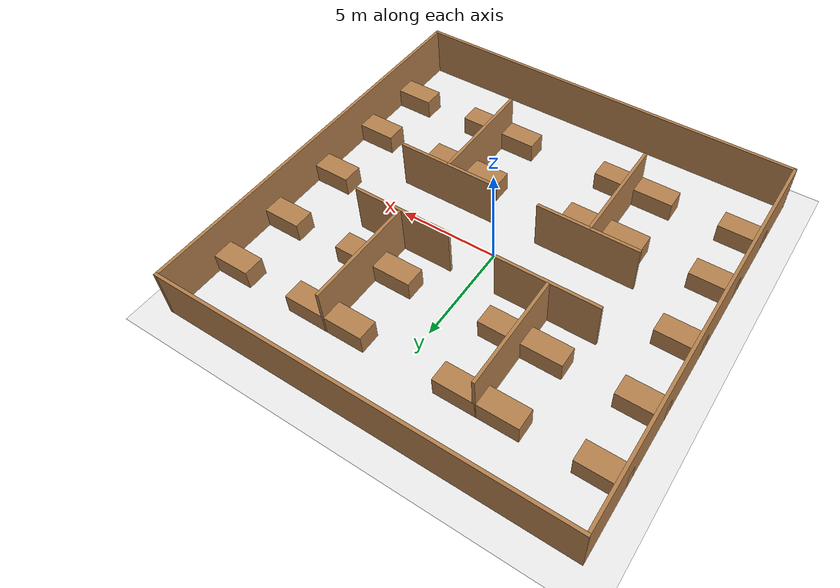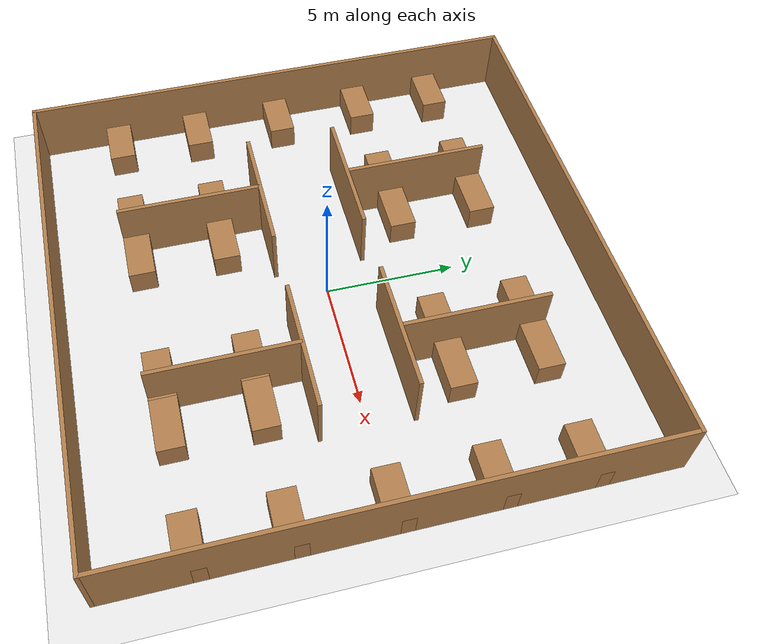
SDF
<sdf version="1.7">
 <world name="default">
  <light name="sun" type="directional">
   <pose>0 0 10 0 -0 0</pose>
   <diffuse>0.8 0.8 0.8 1</diffuse>
   <specular>0.2 0.2 0.2 1</specular>
   <attenuation>
    <range>1000</range>
    <constant>0.9</constant>
    <linear>0.01</linear>
    <quadratic>0.001</quadratic>
   </attenuation>
   <direction>-0.5 0.1 -0.9</direction>
   <spot><inner_angle>0</inner_angle><outer_angle>0</outer_angle><falloff>0</falloff></spot>
  </light>
  <model name="ground_plane">
   <static>1</static>
   <link name="link">
    <collision name="collision">
     <geometry><plane><normal>0 0 1</normal><size>100 100</size></plane></geometry>
     <surface>
      <contact><collide_bitmask>65535</collide_bitmask></contact>
      <friction><ode><mu>100</mu><mu2>50</mu2></ode></friction>
     </surface>
    </collision>
    <visual name="visual">
     <cast_shadows>0</cast_shadows>
     <geometry><plane><normal>0 0 1</normal><size>100 100</size></plane></geometry>
     <material>
      <script><uri>file://media/materials/scripts/gazebo.material</uri><name>Gazebo/White</name></script>
     </material>
    </visual>
   </link>
  </model>
  <gravity>0 0 -9.8</gravity>
  <magnetic_field>6e-06 2.3e-05 -4.2e-05</magnetic_field>
  <atmosphere type="adiabatic"/>
  <physics type="ode">
   <max_step_size>0.001</max_step_size>
   <real_time_factor>1</real_time_factor>
   <real_time_update_rate>1000</real_time_update_rate>
  </physics>
  <scene><ambient>0.4 0.4 0.4 1</ambient><background>0.7 0.7 0.7 1</background><shadows>0</shadows></scene>
  <spherical_coordinates>
   <surface_model>EARTH_WGS84</surface_model>
   <latitude_deg>0</latitude_deg>
   <longitude_deg>0</longitude_deg>
   <elevation>0</elevation>
   <heading_deg>0</heading_deg>
  </spherical_coordinates>
  <model name="warehouse">
   <link name="Wall_10">
    <pose>-1.7 3.65 0 0 0 -1.5708</pose>
    <inertial>
     <mass>1</mass>
     <inertia><ixx>1</ixx><ixy>0</ixy><ixz>0</ixz><iyy>1</iyy><iyz>0</iyz><izz>1</izz></inertia>
    </inertial>
    <visual name="Wall_10_Visual">
     <pose>0 0 1.25 0 -0 0</pose>
     <geometry><box><size>5 0.15 2.5</size></box></geometry>
     <material>
      <script><uri>file://media/materials/scripts/gazebo.material</uri><name>Gazebo/Wood</name></script>
      <ambient>1 1 1 1</ambient>
      <shader type="pixel"><normal_map>__default__</normal_map></shader>
      <diffuse>1 1 1 1</diffuse>
      <specular>0.2 0.2 0.2 1</specular>
      <emissive>0 0 0 1</emissive>
     </material>
     <meta><layer>0</layer></meta>
    </visual>
    <collision name="Wall_10_Collision">
     <pose>0 0 1.25 0 -0 0</pose>
     <geometry><box><size>5 0.15 2.5</size></box></geometry>
     <surface>
      <friction>
       <ode><mu>1</mu><mu2>1</mu2><fdir1>0 0 0</fdir1><slip1>0</slip1><slip2>0</slip2></ode>
       <torsional>
        <coefficient>1</coefficient>
        <patch_radius>0</patch_radius>
        <surface_radius>0</surface_radius>
        <use_patch_radius>1</use_patch_radius>
        <ode><slip>0</slip></ode>
       </torsional>
      </friction>
      <bounce><restitution_coefficient>0</restitution_coefficient><threshold>1e+06</threshold></bounce>
      <contact>
       <collide_without_contact>0</collide_without_contact>
       <collide_without_contact_bitmask>1</collide_without_contact_bitmask>
       <collide_bitmask>1</collide_bitmask>
       <ode>
        <soft_cfm>0</soft_cfm>
        <soft_erp>0.2</soft_erp>
        <kp>1e+13</kp>
        <kd>1</kd>
        <max_vel>0.01</max_vel>
        <min_depth>0</min_depth>
       </ode>
       <bullet>
        <split_impulse>1</split_impulse>
        <split_impulse_penetration_threshold>-0.01</split_impulse_penetration_threshold>
        <soft_cfm>0</soft_cfm>
        <soft_erp>0.2</soft_erp>
        <kp>1e+13</kp>
        <kd>1</kd>
       </bullet>
      </contact>
     </surface>
    </collision>
   </link>
   <link name="Wall_14">
    <pose>-1.7 -3.65 0 0 -0 1.5708</pose>
    <inertial>
     <mass>1</mass>
     <inertia><ixx>1</ixx><ixy>0</ixy><ixz>0</ixz><iyy>1</iyy><iyz>0</iyz><izz>1</izz></inertia>
    </inertial>
    <visual name="Wall_14_Visual">
     <pose>0 0 1.25 0 -0 0</pose>
     <geometry><box><size>5 0.15 2.5</size></box></geometry>
     <material>
      <script><uri>file://media/materials/scripts/gazebo.material</uri><name>Gazebo/Wood</name></script>
      <ambient>1 1 1 1</ambient>
      <shader type="pixel"><normal_map>__default__</normal_map></shader>
      <diffuse>1 1 1 1</diffuse>
      <specular>0.2 0.2 0.2 1</specular>
      <emissive>0 0 0 1</emissive>
     </material>
     <meta><layer>0</layer></meta>
    </visual>
    <collision name="Wall_14_Collision">
     <pose>0 0 1.25 0 -0 0</pose>
     <geometry><box><size>5 0.15 2.5</size></box></geometry>
     <surface>
      <friction>
       <ode><mu>1</mu><mu2>1</mu2><fdir1>0 0 0</fdir1><slip1>0</slip1><slip2>0</slip2></ode>
       <torsional>
        <coefficient>1</coefficient>
        <patch_radius>0</patch_radius>
        <surface_radius>0</surface_radius>
        <use_patch_radius>1</use_patch_radius>
        <ode><slip>0</slip></ode>
       </torsional>
      </friction>
      <bounce><restitution_coefficient>0</restitution_coefficient><threshold>1e+06</threshold></bounce>
      <contact>
       <collide_without_contact>0</collide_without_contact>
       <collide_without_contact_bitmask>1</collide_without_contact_bitmask>
       <collide_bitmask>1</collide_bitmask>
       <ode>
        <soft_cfm>0</soft_cfm>
        <soft_erp>0.2</soft_erp>
        <kp>1e+13</kp>
        <kd>1</kd>
        <max_vel>0.01</max_vel>
        <min_depth>0</min_depth>
       </ode>
       <bullet>
        <split_impulse>1</split_impulse>
        <split_impulse_penetration_threshold>-0.01</split_impulse_penetration_threshold>
        <soft_cfm>0</soft_cfm>
        <soft_erp>0.2</soft_erp>
        <kp>1e+13</kp>
        <kd>1</kd>
       </bullet>
      </contact>
     </surface>
    </collision>
   </link>
   <link name="Wall_18">
    <pose>1.75 -3.65 0 0 -0 1.5708</pose>
    <inertial>
     <mass>1</mass>
     <inertia><ixx>1</ixx><ixy>0</ixy><ixz>0</ixz><iyy>1</iyy><iyz>0</iyz><izz>1</izz></inertia>
    </inertial>
    <visual name="Wall_18_Visual">
     <pose>0 0 1.25 0 -0 0</pose>
     <geometry><box><size>5 0.15 2.5</size></box></geometry>
     <material>
      <script><uri>file://media/materials/scripts/gazebo.material</uri><name>Gazebo/Wood</name></script>
      <ambient>1 1 1 1</ambient>
      <shader type="pixel"><normal_map>__default__</normal_map></shader>
      <diffuse>1 1 1 1</diffuse>
      <specular>0.2 0.2 0.2 1</specular>
      <emissive>0 0 0 1</emissive>
     </material>
     <meta><layer>0</layer></meta>
    </visual>
    <collision name="Wall_18_Collision">
     <pose>0 0 1.25 0 -0 0</pose>
     <geometry><box><size>5 0.15 2.5</size></box></geometry>
     <surface>
      <friction>
       <ode><mu>1</mu><mu2>1</mu2><fdir1>0 0 0</fdir1><slip1>0</slip1><slip2>0</slip2></ode>
       <torsional>
        <coefficient>1</coefficient>
        <patch_radius>0</patch_radius>
        <surface_radius>0</surface_radius>
        <use_patch_radius>1</use_patch_radius>
        <ode><slip>0</slip></ode>
       </torsional>
      </friction>
      <bounce><restitution_coefficient>0</restitution_coefficient><threshold>1e+06</threshold></bounce>
      <contact>
       <collide_without_contact>0</collide_without_contact>
       <collide_without_contact_bitmask>1</collide_without_contact_bitmask>
       <collide_bitmask>1</collide_bitmask>
       <ode>
        <soft_cfm>0</soft_cfm>
        <soft_erp>0.2</soft_erp>
        <kp>1e+13</kp>
        <kd>1</kd>
        <max_vel>0.01</max_vel>
        <min_depth>0</min_depth>
       </ode>
       <bullet>
        <split_impulse>1</split_impulse>
        <split_impulse_penetration_threshold>-0.01</split_impulse_penetration_threshold>
        <soft_cfm>0</soft_cfm>
        <soft_erp>0.2</soft_erp>
        <kp>1e+13</kp>
        <kd>1</kd>
       </bullet>
      </contact>
     </surface>
    </collision>
   </link>
   <link name="Wall_22">
    <pose>1.75 3.65 0 0 0 -1.5708</pose>
    <inertial>
     <mass>1</mass>
     <inertia><ixx>1</ixx><ixy>0</ixy><ixz>0</ixz><iyy>1</iyy><iyz>0</iyz><izz>1</izz></inertia>
    </inertial>
    <visual name="Wall_22_Visual">
     <pose>0 0 1.25 0 -0 0</pose>
     <geometry><box><size>5 0.15 2.5</size></box></geometry>
     <material>
      <script><uri>file://media/materials/scripts/gazebo.material</uri><name>Gazebo/Wood</name></script>
      <ambient>1 1 1 1</ambient>
      <shader type="pixel"><normal_map>__default__</normal_map></shader>
      <diffuse>1 1 1 1</diffuse>
      <specular>0.2 0.2 0.2 1</specular>
      <emissive>0 0 0 1</emissive>
     </material>
     <meta><layer>0</layer></meta>
    </visual>
    <collision name="Wall_22_Collision">
     <pose>0 0 1.25 0 -0 0</pose>
     <geometry><box><size>5 0.15 2.5</size></box></geometry>
     <surface>
      <friction>
       <ode><mu>1</mu><mu2>1</mu2><fdir1>0 0 0</fdir1><slip1>0</slip1><slip2>0</slip2></ode>
       <torsional>
        <coefficient>1</coefficient>
        <patch_radius>0</patch_radius>
        <surface_radius>0</surface_radius>
        <use_patch_radius>1</use_patch_radius>
        <ode><slip>0</slip></ode>
       </torsional>
      </friction>
      <bounce><restitution_coefficient>0</restitution_coefficient><threshold>1e+06</threshold></bounce>
      <contact>
       <collide_without_contact>0</collide_without_contact>
       <collide_without_contact_bitmask>1</collide_without_contact_bitmask>
       <collide_bitmask>1</collide_bitmask>
       <ode>
        <soft_cfm>0</soft_cfm>
        <soft_erp>0.2</soft_erp>
        <kp>1e+13</kp>
        <kd>1</kd>
        <max_vel>0.01</max_vel>
        <min_depth>0</min_depth>
       </ode>
       <bullet>
        <split_impulse>1</split_impulse>
        <split_impulse_penetration_threshold>-0.01</split_impulse_penetration_threshold>
        <soft_cfm>0</soft_cfm>
        <soft_erp>0.2</soft_erp>
        <kp>1e+13</kp>
        <kd>1</kd>
       </bullet>
      </contact>
     </surface>
    </collision>
   </link>
   <link name="Wall_25">
    <pose>-4.5 3.725 0 0 -0 3.14159</pose>
    <inertial>
     <mass>1</mass>
     <inertia><ixx>1</ixx><ixy>0</ixy><ixz>0</ixz><iyy>1</iyy><iyz>0</iyz><izz>1</izz></inertia>
    </inertial>
    <visual name="Wall_25_Visual">
     <pose>0 0 1.25 0 -0 0</pose>
     <geometry><box><size>5.5 0.15 2.5</size></box></geometry>
     <material>
      <script><uri>file://media/materials/scripts/gazebo.material</uri><name>Gazebo/Wood</name></script>
      <ambient>1 1 1 1</ambient>
      <shader type="pixel"><normal_map>__default__</normal_map></shader>
      <diffuse>1 1 1 1</diffuse>
      <specular>0.2 0.2 0.2 1</specular>
      <emissive>0 0 0 1</emissive>
     </material>
     <meta><layer>0</layer></meta>
    </visual>
    <collision name="Wall_25_Collision">
     <pose>0 0 1.25 0 -0 0</pose>
     <geometry><box><size>5.5 0.15 2.5</size></box></geometry>
     <surface>
      <friction>
       <ode><mu>1</mu><mu2>1</mu2><fdir1>0 0 0</fdir1><slip1>0</slip1><slip2>0</slip2></ode>
       <torsional>
        <coefficient>1</coefficient>
        <patch_radius>0</patch_radius>
        <surface_radius>0</surface_radius>
        <use_patch_radius>1</use_patch_radius>
        <ode><slip>0</slip></ode>
       </torsional>
      </friction>
      <bounce><restitution_coefficient>0</restitution_coefficient><threshold>1e+06</threshold></bounce>
      <contact>
       <collide_without_contact>0</collide_without_contact>
       <collide_without_contact_bitmask>1</collide_without_contact_bitmask>
       <collide_bitmask>1</collide_bitmask>
       <ode>
        <soft_cfm>0</soft_cfm>
        <soft_erp>0.2</soft_erp>
        <kp>1e+13</kp>
        <kd>1</kd>
        <max_vel>0.01</max_vel>
        <min_depth>0</min_depth>
       </ode>
       <bullet>
        <split_impulse>1</split_impulse>
        <split_impulse_penetration_threshold>-0.01</split_impulse_penetration_threshold>
        <soft_cfm>0</soft_cfm>
        <soft_erp>0.2</soft_erp>
        <kp>1e+13</kp>
        <kd>1</kd>
       </bullet>
      </contact>
     </surface>
    </collision>
   </link>
   <link name="Wall_28">
    <pose>-4.5 -3.725 0 0 -0 3.14159</pose>
    <inertial>
     <mass>1</mass>
     <inertia><ixx>1</ixx><ixy>0</ixy><ixz>0</ixz><iyy>1</iyy><iyz>0</iyz><izz>1</izz></inertia>
    </inertial>
    <visual name="Wall_28_Visual">
     <pose>0 0 1.25 0 -0 0</pose>
     <geometry><box><size>5.5 0.15 2.5</size></box></geometry>
     <material>
      <script><uri>file://media/materials/scripts/gazebo.material</uri><name>Gazebo/Wood</name></script>
      <ambient>1 1 1 1</ambient>
      <shader type="pixel"><normal_map>__default__</normal_map></shader>
      <diffuse>1 1 1 1</diffuse>
      <specular>0.2 0.2 0.2 1</specular>
      <emissive>0 0 0 1</emissive>
     </material>
     <meta><layer>0</layer></meta>
    </visual>
    <collision name="Wall_28_Collision">
     <pose>0 0 1.25 0 -0 0</pose>
     <geometry><box><size>5.5 0.15 2.5</size></box></geometry>
     <surface>
      <friction>
       <ode><mu>1</mu><mu2>1</mu2><fdir1>0 0 0</fdir1><slip1>0</slip1><slip2>0</slip2></ode>
       <torsional>
        <coefficient>1</coefficient>
        <patch_radius>0</patch_radius>
        <surface_radius>0</surface_radius>
        <use_patch_radius>1</use_patch_radius>
        <ode><slip>0</slip></ode>
       </torsional>
      </friction>
      <bounce><restitution_coefficient>0</restitution_coefficient><threshold>1e+06</threshold></bounce>
      <contact>
       <collide_without_contact>0</collide_without_contact>
       <collide_without_contact_bitmask>1</collide_without_contact_bitmask>
       <collide_bitmask>1</collide_bitmask>
       <ode>
        <soft_cfm>0</soft_cfm>
        <soft_erp>0.2</soft_erp>
        <kp>1e+13</kp>
        <kd>1</kd>
        <max_vel>0.01</max_vel>
        <min_depth>0</min_depth>
       </ode>
       <bullet>
        <split_impulse>1</split_impulse>
        <split_impulse_penetration_threshold>-0.01</split_impulse_penetration_threshold>
        <soft_cfm>0</soft_cfm>
        <soft_erp>0.2</soft_erp>
        <kp>1e+13</kp>
        <kd>1</kd>
       </bullet>
      </contact>
     </surface>
    </collision>
   </link>
   <link name="Wall_3">
    <pose>-9.925 0 0 0 0 -1.5708</pose>
    <visual name="Wall_3_Visual">
     <pose>0 0 1.25 0 -0 0</pose>
     <geometry><box><size>20 0.15 2.5</size></box></geometry>
     <material>
      <script><uri>file://media/materials/scripts/gazebo.material</uri><name>Gazebo/Wood</name></script>
      <ambient>1 1 1 1</ambient>
      <shader type="pixel"/>
     </material>
     <meta><layer>0</layer></meta>
    </visual>
    <collision name="Wall_3_Collision">
     <pose>0 0 1.25 0 -0 0</pose>
     <geometry><box><size>20 0.15 2.5</size></box></geometry>
     <surface>
      <friction>
       <ode><mu>1</mu><mu2>1</mu2><fdir1>0 0 0</fdir1><slip1>0</slip1><slip2>0</slip2></ode>
       <torsional>
        <coefficient>1</coefficient>
        <patch_radius>0</patch_radius>
        <surface_radius>0</surface_radius>
        <use_patch_radius>1</use_patch_radius>
        <ode><slip>0</slip></ode>
       </torsional>
      </friction>
      <bounce><restitution_coefficient>0</restitution_coefficient><threshold>1e+06</threshold></bounce>
      <contact>
       <collide_without_contact>0</collide_without_contact>
       <collide_without_contact_bitmask>1</collide_without_contact_bitmask>
       <collide_bitmask>1</collide_bitmask>
       <ode>
        <soft_cfm>0</soft_cfm>
        <soft_erp>0.2</soft_erp>
        <kp>1e+13</kp>
        <kd>1</kd>
        <max_vel>0.01</max_vel>
        <min_depth>0</min_depth>
       </ode>
       <bullet>
        <split_impulse>1</split_impulse>
        <split_impulse_penetration_threshold>-0.01</split_impulse_penetration_threshold>
        <soft_cfm>0</soft_cfm>
        <soft_erp>0.2</soft_erp>
        <kp>1e+13</kp>
        <kd>1</kd>
       </bullet>
      </contact>
     </surface>
    </collision>
   </link>
   <link name="Wall_31">
    <pose>4.5 -3.725 0 0 -0 0</pose>
    <inertial>
     <mass>1</mass>
     <inertia><ixx>1</ixx><ixy>0</ixy><ixz>0</ixz><iyy>1</iyy><iyz>0</iyz><izz>1</izz></inertia>
    </inertial>
    <visual name="Wall_31_Visual">
     <pose>0 0 1.25 0 -0 0</pose>
     <geometry><box><size>5.5 0.15 2.5</size></box></geometry>
     <material>
      <script><uri>file://media/materials/scripts/gazebo.material</uri><name>Gazebo/Wood</name></script>
      <ambient>1 1 1 1</ambient>
      <shader type="pixel"><normal_map>__default__</normal_map></shader>
      <diffuse>1 1 1 1</diffuse>
      <specular>0.2 0.2 0.2 1</specular>
      <emissive>0 0 0 1</emissive>
     </material>
     <meta><layer>0</layer></meta>
    </visual>
    <collision name="Wall_31_Collision">
     <pose>0 0 1.25 0 -0 0</pose>
     <geometry><box><size>5.5 0.15 2.5</size></box></geometry>
     <surface>
      <friction>
       <ode><mu>1</mu><mu2>1</mu2><fdir1>0 0 0</fdir1><slip1>0</slip1><slip2>0</slip2></ode>
       <torsional>
        <coefficient>1</coefficient>
        <patch_radius>0</patch_radius>
        <surface_radius>0</surface_radius>
        <use_patch_radius>1</use_patch_radius>
        <ode><slip>0</slip></ode>
       </torsional>
      </friction>
      <bounce><restitution_coefficient>0</restitution_coefficient><threshold>1e+06</threshold></bounce>
      <contact>
       <collide_without_contact>0</collide_without_contact>
       <collide_without_contact_bitmask>1</collide_without_contact_bitmask>
       <collide_bitmask>1</collide_bitmask>
       <ode>
        <soft_cfm>0</soft_cfm>
        <soft_erp>0.2</soft_erp>
        <kp>1e+13</kp>
        <kd>1</kd>
        <max_vel>0.01</max_vel>
        <min_depth>0</min_depth>
       </ode>
       <bullet>
        <split_impulse>1</split_impulse>
        <split_impulse_penetration_threshold>-0.01</split_impulse_penetration_threshold>
        <soft_cfm>0</soft_cfm>
        <soft_erp>0.2</soft_erp>
        <kp>1e+13</kp>
        <kd>1</kd>
       </bullet>
      </contact>
     </surface>
    </collision>
   </link>
   <link name="Wall_34">
    <pose>4.5 3.575 0 0 -0 0</pose>
    <inertial>
     <mass>1</mass>
     <inertia><ixx>1</ixx><ixy>0</ixy><ixz>0</ixz><iyy>1</iyy><iyz>0</iyz><izz>1</izz></inertia>
    </inertial>
    <visual name="Wall_34_Visual">
     <pose>0 0 1.25 0 -0 0</pose>
     <geometry><box><size>5.5 0.15 2.5</size></box></geometry>
     <material>
      <script><uri>file://media/materials/scripts/gazebo.material</uri><name>Gazebo/Wood</name></script>
      <ambient>1 1 1 1</ambient>
      <shader type="pixel"><normal_map>__default__</normal_map></shader>
      <diffuse>1 1 1 1</diffuse>
      <specular>0.2 0.2 0.2 1</specular>
      <emissive>0 0 0 1</emissive>
     </material>
     <meta><layer>0</layer></meta>
    </visual>
    <collision name="Wall_34_Collision">
     <pose>0 0 1.25 0 -0 0</pose>
     <geometry><box><size>5.5 0.15 2.5</size></box></geometry>
     <surface>
      <friction>
       <ode><mu>1</mu><mu2>1</mu2><fdir1>0 0 0</fdir1><slip1>0</slip1><slip2>0</slip2></ode>
       <torsional>
        <coefficient>1</coefficient>
        <patch_radius>0</patch_radius>
        <surface_radius>0</surface_radius>
        <use_patch_radius>1</use_patch_radius>
        <ode><slip>0</slip></ode>
       </torsional>
      </friction>
      <bounce><restitution_coefficient>0</restitution_coefficient><threshold>1e+06</threshold></bounce>
      <contact>
       <collide_without_contact>0</collide_without_contact>
       <collide_without_contact_bitmask>1</collide_without_contact_bitmask>
       <collide_bitmask>1</collide_bitmask>
       <ode>
        <soft_cfm>0</soft_cfm>
        <soft_erp>0.2</soft_erp>
        <kp>1e+13</kp>
        <kd>1</kd>
        <max_vel>0.01</max_vel>
        <min_depth>0</min_depth>
       </ode>
       <bullet>
        <split_impulse>1</split_impulse>
        <split_impulse_penetration_threshold>-0.01</split_impulse_penetration_threshold>
        <soft_cfm>0</soft_cfm>
        <soft_erp>0.2</soft_erp>
        <kp>1e+13</kp>
        <kd>1</kd>
       </bullet>
      </contact>
     </surface>
    </collision>
   </link>
   <link name="Wall_4">
    <pose>-0 -9.925 0 0 -0 0</pose>
    <visual name="Wall_4_Visual">
     <pose>0 0 1.25 0 -0 0</pose>
     <geometry><box><size>20 0.15 2.5</size></box></geometry>
     <material>
      <script><uri>file://media/materials/scripts/gazebo.material</uri><name>Gazebo/Wood</name></script>
      <ambient>1 1 1 1</ambient>
      <shader type="pixel"/>
     </material>
     <meta><layer>0</layer></meta>
    </visual>
    <collision name="Wall_4_Collision">
     <pose>0 0 1.25 0 -0 0</pose>
     <geometry><box><size>20 0.15 2.5</size></box></geometry>
     <surface>
      <friction>
       <ode><mu>1</mu><mu2>1</mu2><fdir1>0 0 0</fdir1><slip1>0</slip1><slip2>0</slip2></ode>
       <torsional>
        <coefficient>1</coefficient>
        <patch_radius>0</patch_radius>
        <surface_radius>0</surface_radius>
        <use_patch_radius>1</use_patch_radius>
        <ode><slip>0</slip></ode>
       </torsional>
      </friction>
      <bounce><restitution_coefficient>0</restitution_coefficient><threshold>1e+06</threshold></bounce>
      <contact>
       <collide_without_contact>0</collide_without_contact>
       <collide_without_contact_bitmask>1</collide_without_contact_bitmask>
       <collide_bitmask>1</collide_bitmask>
       <ode>
        <soft_cfm>0</soft_cfm>
        <soft_erp>0.2</soft_erp>
        <kp>1e+13</kp>
        <kd>1</kd>
        <max_vel>0.01</max_vel>
        <min_depth>0</min_depth>
       </ode>
       <bullet>
        <split_impulse>1</split_impulse>
        <split_impulse_penetration_threshold>-0.01</split_impulse_penetration_threshold>
        <soft_cfm>0</soft_cfm>
        <soft_erp>0.2</soft_erp>
        <kp>1e+13</kp>
        <kd>1</kd>
       </bullet>
      </contact>
     </surface>
    </collision>
   </link>
   <link name="Wall_5">
    <pose>9.925 -0 0 0 -0 1.5708</pose>
    <visual name="Wall_5_Visual">
     <pose>0 0 1.25 0 -0 0</pose>
     <geometry><box><size>20 0.15 2.5</size></box></geometry>
     <material>
      <script><uri>file://media/materials/scripts/gazebo.material</uri><name>Gazebo/Wood</name></script>
      <ambient>1 1 1 1</ambient>
      <shader type="pixel"/>
     </material>
     <meta><layer>0</layer></meta>
    </visual>
    <collision name="Wall_5_Collision">
     <pose>0 0 1.25 0 -0 0</pose>
     <geometry><box><size>20 0.15 2.5</size></box></geometry>
     <surface>
      <friction>
       <ode><mu>1</mu><mu2>1</mu2><fdir1>0 0 0</fdir1><slip1>0</slip1><slip2>0</slip2></ode>
       <torsional>
        <coefficient>1</coefficient>
        <patch_radius>0</patch_radius>
        <surface_radius>0</surface_radius>
        <use_patch_radius>1</use_patch_radius>
        <ode><slip>0</slip></ode>
       </torsional>
      </friction>
      <bounce><restitution_coefficient>0</restitution_coefficient><threshold>1e+06</threshold></bounce>
      <contact>
       <collide_without_contact>0</collide_without_contact>
       <collide_without_contact_bitmask>1</collide_without_contact_bitmask>
       <collide_bitmask>1</collide_bitmask>
       <ode>
        <soft_cfm>0</soft_cfm>
        <soft_erp>0.2</soft_erp>
        <kp>1e+13</kp>
        <kd>1</kd>
        <max_vel>0.01</max_vel>
        <min_depth>0</min_depth>
       </ode>
       <bullet>
        <split_impulse>1</split_impulse>
        <split_impulse_penetration_threshold>-0.01</split_impulse_penetration_threshold>
        <soft_cfm>0</soft_cfm>
        <soft_erp>0.2</soft_erp>
        <kp>1e+13</kp>
        <kd>1</kd>
       </bullet>
      </contact>
     </surface>
    </collision>
   </link>
   <link name="Wall_6">
    <pose>0 9.925 0 0 -0 3.14159</pose>
    <visual name="Wall_6_Visual">
     <pose>0 0 1.25 0 -0 0</pose>
     <geometry><box><size>20 0.15 2.5</size></box></geometry>
     <material>
      <script><uri>file://media/materials/scripts/gazebo.material</uri><name>Gazebo/Wood</name></script>
      <ambient>1 1 1 1</ambient>
      <shader type="pixel"/>
     </material>
     <meta><layer>0</layer></meta>
    </visual>
    <collision name="Wall_6_Collision">
     <pose>0 0 1.25 0 -0 0</pose>
     <geometry><box><size>20 0.15 2.5</size></box></geometry>
     <surface>
      <friction>
       <ode><mu>1</mu><mu2>1</mu2><fdir1>0 0 0</fdir1><slip1>0</slip1><slip2>0</slip2></ode>
       <torsional>
        <coefficient>1</coefficient>
        <patch_radius>0</patch_radius>
        <surface_radius>0</surface_radius>
        <use_patch_radius>1</use_patch_radius>
        <ode><slip>0</slip></ode>
       </torsional>
      </friction>
      <bounce><restitution_coefficient>0</restitution_coefficient><threshold>1e+06</threshold></bounce>
      <contact>
       <collide_without_contact>0</collide_without_contact>
       <collide_without_contact_bitmask>1</collide_without_contact_bitmask>
       <collide_bitmask>1</collide_bitmask>
       <ode>
        <soft_cfm>0</soft_cfm>
        <soft_erp>0.2</soft_erp>
        <kp>1e+13</kp>
        <kd>1</kd>
        <max_vel>0.01</max_vel>
        <min_depth>0</min_depth>
       </ode>
       <bullet>
        <split_impulse>1</split_impulse>
        <split_impulse_penetration_threshold>-0.01</split_impulse_penetration_threshold>
        <soft_cfm>0</soft_cfm>
        <soft_erp>0.2</soft_erp>
        <kp>1e+13</kp>
        <kd>1</kd>
       </bullet>
      </contact>
     </surface>
    </collision>
   </link>
   <link name="link_1_clone">
    <inertial>
     <mass>1</mass>
     <inertia>
      <ixx>0.166667</ixx>
      <ixy>0</ixy>
      <ixz>0</ixz>
      <iyy>0.166667</iyy>
      <iyz>0</iyz>
      <izz>0.166667</izz>
     </inertia>
    </inertial>
    <pose>-0 -9 0.5 0 -0 3.14</pose>
    <visual name="visual">
     <geometry><box><size>1 2 1</size></box></geometry>
     <material>
      <lighting>1</lighting>
      <script><uri>file://media/materials/scripts/gazebo.material</uri><name>Gazebo/Wood</name></script>
      <shader type="pixel"><normal_map>__default__</normal_map></shader>
      <ambient>0.3 0.3 0.3 1</ambient>
      <diffuse>0.7 0.7 0.7 1</diffuse>
      <specular>0.01 0.01 0.01 1</specular>
      <emissive>0 0 0 1</emissive>
     </material>
    </visual>
    <collision name="collision">
     <geometry><box><size>1 2 1</size></box></geometry>
     <surface>
      <friction>
       <ode><mu>1</mu><mu2>1</mu2><fdir1>0 0 0</fdir1><slip1>0</slip1><slip2>0</slip2></ode>
       <torsional>
        <coefficient>1</coefficient>
        <patch_radius>0</patch_radius>
        <surface_radius>0</surface_radius>
        <use_patch_radius>1</use_patch_radius>
        <ode><slip>0</slip></ode>
       </torsional>
      </friction>
      <bounce><restitution_coefficient>0</restitution_coefficient><threshold>1e+06</threshold></bounce>
      <contact>
       <collide_without_contact>0</collide_without_contact>
       <collide_without_contact_bitmask>1</collide_without_contact_bitmask>
       <collide_bitmask>1</collide_bitmask>
       <ode>
        <soft_cfm>0</soft_cfm>
        <soft_erp>0.2</soft_erp>
        <kp>1e+13</kp>
        <kd>1</kd>
        <max_vel>0.01</max_vel>
        <min_depth>0</min_depth>
       </ode>
       <bullet>
        <split_impulse>1</split_impulse>
        <split_impulse_penetration_threshold>-0.01</split_impulse_penetration_threshold>
        <soft_cfm>0</soft_cfm>
        <soft_erp>0.2</soft_erp>
        <kp>1e+13</kp>
        <kd>1</kd>
       </bullet>
      </contact>
     </surface>
    </collision>
   </link>
   <link name="link_1_clone_0">
    <inertial>
     <mass>1</mass>
     <inertia>
      <ixx>0.166667</ixx>
      <ixy>0</ixy>
      <ixz>0</ixz>
      <iyy>0.166667</iyy>
      <iyz>0</iyz>
      <izz>0.166667</izz>
     </inertia>
    </inertial>
    <pose>3.5 -9 0.5 0 -0 3.14</pose>
    <visual name="visual">
     <geometry><box><size>1 2 1</size></box></geometry>
     <material>
      <lighting>1</lighting>
      <script><uri>file://media/materials/scripts/gazebo.material</uri><name>Gazebo/Wood</name></script>
      <shader type="pixel"><normal_map>__default__</normal_map></shader>
      <ambient>0.3 0.3 0.3 1</ambient>
      <diffuse>0.7 0.7 0.7 1</diffuse>
      <specular>0.01 0.01 0.01 1</specular>
      <emissive>0 0 0 1</emissive>
     </material>
    </visual>
    <collision name="collision">
     <geometry><box><size>1 2 1</size></box></geometry>
     <surface>
      <friction>
       <ode><mu>1</mu><mu2>1</mu2><fdir1>0 0 0</fdir1><slip1>0</slip1><slip2>0</slip2></ode>
       <torsional>
        <coefficient>1</coefficient>
        <patch_radius>0</patch_radius>
        <surface_radius>0</surface_radius>
        <use_patch_radius>1</use_patch_radius>
        <ode><slip>0</slip></ode>
       </torsional>
      </friction>
      <bounce><restitution_coefficient>0</restitution_coefficient><threshold>1e+06</threshold></bounce>
      <contact>
       <collide_without_contact>0</collide_without_contact>
       <collide_without_contact_bitmask>1</collide_without_contact_bitmask>
       <collide_bitmask>1</collide_bitmask>
       <ode>
        <soft_cfm>0</soft_cfm>
        <soft_erp>0.2</soft_erp>
        <kp>1e+13</kp>
        <kd>1</kd>
        <max_vel>0.01</max_vel>
        <min_depth>0</min_depth>
       </ode>
       <bullet>
        <split_impulse>1</split_impulse>
        <split_impulse_penetration_threshold>-0.01</split_impulse_penetration_threshold>
        <soft_cfm>0</soft_cfm>
        <soft_erp>0.2</soft_erp>
        <kp>1e+13</kp>
        <kd>1</kd>
       </bullet>
      </contact>
     </surface>
    </collision>
   </link>
   <link name="link_1_clone_1">
    <inertial>
     <mass>1</mass>
     <inertia>
      <ixx>0.166667</ixx>
      <ixy>0</ixy>
      <ixz>0</ixz>
      <iyy>0.166667</iyy>
      <iyz>0</iyz>
      <izz>0.166667</izz>
     </inertia>
    </inertial>
    <pose>6.75 -9 0.5 0 -0 3.14</pose>
    <visual name="visual">
     <geometry><box><size>1 2 1</size></box></geometry>
     <material>
      <lighting>1</lighting>
      <script><uri>file://media/materials/scripts/gazebo.material</uri><name>Gazebo/Wood</name></script>
      <shader type="pixel"><normal_map>__default__</normal_map></shader>
      <ambient>0.3 0.3 0.3 1</ambient>
      <diffuse>0.7 0.7 0.7 1</diffuse>
      <specular>0.01 0.01 0.01 1</specular>
      <emissive>0 0 0 1</emissive>
     </material>
    </visual>
    <collision name="collision">
     <geometry><box><size>1 2 1</size></box></geometry>
     <surface>
      <friction>
       <ode><mu>1</mu><mu2>1</mu2><fdir1>0 0 0</fdir1><slip1>0</slip1><slip2>0</slip2></ode>
       <torsional>
        <coefficient>1</coefficient>
        <patch_radius>0</patch_radius>
        <surface_radius>0</surface_radius>
        <use_patch_radius>1</use_patch_radius>
        <ode><slip>0</slip></ode>
       </torsional>
      </friction>
      <bounce><restitution_coefficient>0</restitution_coefficient><threshold>1e+06</threshold></bounce>
      <contact>
       <collide_without_contact>0</collide_without_contact>
       <collide_without_contact_bitmask>1</collide_without_contact_bitmask>
       <collide_bitmask>1</collide_bitmask>
       <ode>
        <soft_cfm>0</soft_cfm>
        <soft_erp>0.2</soft_erp>
        <kp>1e+13</kp>
        <kd>1</kd>
        <max_vel>0.01</max_vel>
        <min_depth>0</min_depth>
       </ode>
       <bullet>
        <split_impulse>1</split_impulse>
        <split_impulse_penetration_threshold>-0.01</split_impulse_penetration_threshold>
        <soft_cfm>0</soft_cfm>
        <soft_erp>0.2</soft_erp>
        <kp>1e+13</kp>
        <kd>1</kd>
       </bullet>
      </contact>
     </surface>
    </collision>
   </link>
   <link name="link_1_clone_10">
    <inertial>
     <mass>1</mass>
     <inertia>
      <ixx>0.166667</ixx>
      <ixy>0</ixy>
      <ixz>0</ixz>
      <iyy>0.166667</iyy>
      <iyz>0</iyz>
      <izz>0.166667</izz>
     </inertia>
    </inertial>
    <pose>3.5 -4.75 0.5 0 -0 3.14</pose>
    <visual name="visual">
     <geometry><box><size>1 2 1</size></box></geometry>
     <material>
      <lighting>1</lighting>
      <script><uri>file://media/materials/scripts/gazebo.material</uri><name>Gazebo/Wood</name></script>
      <shader type="pixel"><normal_map>__default__</normal_map></shader>
      <ambient>0.3 0.3 0.3 1</ambient>
      <diffuse>0.7 0.7 0.7 1</diffuse>
      <specular>0.01 0.01 0.01 1</specular>
      <emissive>0 0 0 1</emissive>
     </material>
    </visual>
    <collision name="collision">
     <geometry><box><size>1 2 1</size></box></geometry>
     <surface>
      <friction>
       <ode><mu>1</mu><mu2>1</mu2><fdir1>0 0 0</fdir1><slip1>0</slip1><slip2>0</slip2></ode>
       <torsional>
        <coefficient>1</coefficient>
        <patch_radius>0</patch_radius>
        <surface_radius>0</surface_radius>
        <use_patch_radius>1</use_patch_radius>
        <ode><slip>0</slip></ode>
       </torsional>
      </friction>
      <bounce><restitution_coefficient>0</restitution_coefficient><threshold>1e+06</threshold></bounce>
      <contact>
       <collide_without_contact>0</collide_without_contact>
       <collide_without_contact_bitmask>1</collide_without_contact_bitmask>
       <collide_bitmask>1</collide_bitmask>
       <ode>
        <soft_cfm>0</soft_cfm>
        <soft_erp>0.2</soft_erp>
        <kp>1e+13</kp>
        <kd>1</kd>
        <max_vel>0.01</max_vel>
        <min_depth>0</min_depth>
       </ode>
       <bullet>
        <split_impulse>1</split_impulse>
        <split_impulse_penetration_threshold>-0.01</split_impulse_penetration_threshold>
        <soft_cfm>0</soft_cfm>
        <soft_erp>0.2</soft_erp>
        <kp>1e+13</kp>
        <kd>1</kd>
       </bullet>
      </contact>
     </surface>
    </collision>
   </link>
   <link name="link_1_clone_11">
    <inertial>
     <mass>1</mass>
     <inertia>
      <ixx>0.166667</ixx>
      <ixy>0</ixy>
      <ixz>0</ixz>
      <iyy>0.166667</iyy>
      <iyz>0</iyz>
      <izz>0.166667</izz>
     </inertia>
    </inertial>
    <pose>6.75305 -4.75 0.5 0 -0 3.14</pose>
    <visual name="visual">
     <geometry><box><size>1 2 1</size></box></geometry>
     <material>
      <lighting>1</lighting>
      <script><uri>file://media/materials/scripts/gazebo.material</uri><name>Gazebo/Wood</name></script>
      <shader type="pixel"><normal_map>__default__</normal_map></shader>
      <ambient>0.3 0.3 0.3 1</ambient>
      <diffuse>0.7 0.7 0.7 1</diffuse>
      <specular>0.01 0.01 0.01 1</specular>
      <emissive>0 0 0 1</emissive>
     </material>
    </visual>
    <collision name="collision">
     <geometry><box><size>1 2 1</size></box></geometry>
     <surface>
      <friction>
       <ode><mu>1</mu><mu2>1</mu2><fdir1>0 0 0</fdir1><slip1>0</slip1><slip2>0</slip2></ode>
       <torsional>
        <coefficient>1</coefficient>
        <patch_radius>0</patch_radius>
        <surface_radius>0</surface_radius>
        <use_patch_radius>1</use_patch_radius>
        <ode><slip>0</slip></ode>
       </torsional>
      </friction>
      <bounce><restitution_coefficient>0</restitution_coefficient><threshold>1e+06</threshold></bounce>
      <contact>
       <collide_without_contact>0</collide_without_contact>
       <collide_without_contact_bitmask>1</collide_without_contact_bitmask>
       <collide_bitmask>1</collide_bitmask>
       <ode>
        <soft_cfm>0</soft_cfm>
        <soft_erp>0.2</soft_erp>
        <kp>1e+13</kp>
        <kd>1</kd>
        <max_vel>0.01</max_vel>
        <min_depth>0</min_depth>
       </ode>
       <bullet>
        <split_impulse>1</split_impulse>
        <split_impulse_penetration_threshold>-0.01</split_impulse_penetration_threshold>
        <soft_cfm>0</soft_cfm>
        <soft_erp>0.2</soft_erp>
        <kp>1e+13</kp>
        <kd>1</kd>
       </bullet>
      </contact>
     </surface>
    </collision>
   </link>
   <link name="link_1_clone_12">
    <inertial>
     <mass>1</mass>
     <inertia>
      <ixx>0.166667</ixx>
      <ixy>0</ixy>
      <ixz>0</ixz>
      <iyy>0.166667</iyy>
      <iyz>0</iyz>
      <izz>0.166667</izz>
     </inertia>
    </inertial>
    <pose>-6.75 4.75 0.5 0 -0 3.14</pose>
    <visual name="visual">
     <geometry><box><size>1 2 1</size></box></geometry>
     <material>
      <lighting>1</lighting>
      <script><uri>file://media/materials/scripts/gazebo.material</uri><name>Gazebo/Wood</name></script>
      <shader type="pixel"><normal_map>__default__</normal_map></shader>
      <ambient>0.3 0.3 0.3 1</ambient>
      <diffuse>0.7 0.7 0.7 1</diffuse>
      <specular>0.01 0.01 0.01 1</specular>
      <emissive>0 0 0 1</emissive>
     </material>
    </visual>
    <collision name="collision">
     <geometry><box><size>1 2 1</size></box></geometry>
     <surface>
      <friction>
       <ode><mu>1</mu><mu2>1</mu2><fdir1>0 0 0</fdir1><slip1>0</slip1><slip2>0</slip2></ode>
       <torsional>
        <coefficient>1</coefficient>
        <patch_radius>0</patch_radius>
        <surface_radius>0</surface_radius>
        <use_patch_radius>1</use_patch_radius>
        <ode><slip>0</slip></ode>
       </torsional>
      </friction>
      <bounce><restitution_coefficient>0</restitution_coefficient><threshold>1e+06</threshold></bounce>
      <contact>
       <collide_without_contact>0</collide_without_contact>
       <collide_without_contact_bitmask>1</collide_without_contact_bitmask>
       <collide_bitmask>1</collide_bitmask>
       <ode>
        <soft_cfm>0</soft_cfm>
        <soft_erp>0.2</soft_erp>
        <kp>1e+13</kp>
        <kd>1</kd>
        <max_vel>0.01</max_vel>
        <min_depth>0</min_depth>
       </ode>
       <bullet>
        <split_impulse>1</split_impulse>
        <split_impulse_penetration_threshold>-0.01</split_impulse_penetration_threshold>
        <soft_cfm>0</soft_cfm>
        <soft_erp>0.2</soft_erp>
        <kp>1e+13</kp>
        <kd>1</kd>
       </bullet>
      </contact>
     </surface>
    </collision>
   </link>
   <link name="link_1_clone_13">
    <inertial>
     <mass>1</mass>
     <inertia>
      <ixx>0.166667</ixx>
      <ixy>0</ixy>
      <ixz>0</ixz>
      <iyy>0.166667</iyy>
      <iyz>0</iyz>
      <izz>0.166667</izz>
     </inertia>
    </inertial>
    <pose>-3.5 4.75 0.5 0 -0 3.14</pose>
    <visual name="visual">
     <geometry><box><size>1 2 1</size></box></geometry>
     <material>
      <lighting>1</lighting>
      <script><uri>file://media/materials/scripts/gazebo.material</uri><name>Gazebo/Wood</name></script>
      <shader type="pixel"><normal_map>__default__</normal_map></shader>
      <ambient>0.3 0.3 0.3 1</ambient>
      <diffuse>0.7 0.7 0.7 1</diffuse>
      <specular>0.01 0.01 0.01 1</specular>
      <emissive>0 0 0 1</emissive>
     </material>
    </visual>
    <collision name="collision">
     <geometry><box><size>1 2 1</size></box></geometry>
     <surface>
      <friction>
       <ode><mu>1</mu><mu2>1</mu2><fdir1>0 0 0</fdir1><slip1>0</slip1><slip2>0</slip2></ode>
       <torsional>
        <coefficient>1</coefficient>
        <patch_radius>0</patch_radius>
        <surface_radius>0</surface_radius>
        <use_patch_radius>1</use_patch_radius>
        <ode><slip>0</slip></ode>
       </torsional>
      </friction>
      <bounce><restitution_coefficient>0</restitution_coefficient><threshold>1e+06</threshold></bounce>
      <contact>
       <collide_without_contact>0</collide_without_contact>
       <collide_without_contact_bitmask>1</collide_without_contact_bitmask>
       <collide_bitmask>1</collide_bitmask>
       <ode>
        <soft_cfm>0</soft_cfm>
        <soft_erp>0.2</soft_erp>
        <kp>1e+13</kp>
        <kd>1</kd>
        <max_vel>0.01</max_vel>
        <min_depth>0</min_depth>
       </ode>
       <bullet>
        <split_impulse>1</split_impulse>
        <split_impulse_penetration_threshold>-0.01</split_impulse_penetration_threshold>
        <soft_cfm>0</soft_cfm>
        <soft_erp>0.2</soft_erp>
        <kp>1e+13</kp>
        <kd>1</kd>
       </bullet>
      </contact>
     </surface>
    </collision>
   </link>
   <link name="link_1_clone_14">
    <inertial>
     <mass>1</mass>
     <inertia>
      <ixx>0.166667</ixx>
      <ixy>0</ixy>
      <ixz>0</ixz>
      <iyy>0.166667</iyy>
      <iyz>0</iyz>
      <izz>0.166667</izz>
     </inertia>
    </inertial>
    <pose>3.5 4.75 0.5 0 -0 3.14</pose>
    <visual name="visual">
     <geometry><box><size>1 2 1</size></box></geometry>
     <material>
      <lighting>1</lighting>
      <script><uri>file://media/materials/scripts/gazebo.material</uri><name>Gazebo/Wood</name></script>
      <shader type="pixel"><normal_map>__default__</normal_map></shader>
      <ambient>0.3 0.3 0.3 1</ambient>
      <diffuse>0.7 0.7 0.7 1</diffuse>
      <specular>0.01 0.01 0.01 1</specular>
      <emissive>0 0 0 1</emissive>
     </material>
    </visual>
    <collision name="collision">
     <geometry><box><size>1 2 1</size></box></geometry>
     <surface>
      <friction>
       <ode><mu>1</mu><mu2>1</mu2><fdir1>0 0 0</fdir1><slip1>0</slip1><slip2>0</slip2></ode>
       <torsional>
        <coefficient>1</coefficient>
        <patch_radius>0</patch_radius>
        <surface_radius>0</surface_radius>
        <use_patch_radius>1</use_patch_radius>
        <ode><slip>0</slip></ode>
       </torsional>
      </friction>
      <bounce><restitution_coefficient>0</restitution_coefficient><threshold>1e+06</threshold></bounce>
      <contact>
       <collide_without_contact>0</collide_without_contact>
       <collide_without_contact_bitmask>1</collide_without_contact_bitmask>
       <collide_bitmask>1</collide_bitmask>
       <ode>
        <soft_cfm>0</soft_cfm>
        <soft_erp>0.2</soft_erp>
        <kp>1e+13</kp>
        <kd>1</kd>
        <max_vel>0.01</max_vel>
        <min_depth>0</min_depth>
       </ode>
       <bullet>
        <split_impulse>1</split_impulse>
        <split_impulse_penetration_threshold>-0.01</split_impulse_penetration_threshold>
        <soft_cfm>0</soft_cfm>
        <soft_erp>0.2</soft_erp>
        <kp>1e+13</kp>
        <kd>1</kd>
       </bullet>
      </contact>
     </surface>
    </collision>
   </link>
   <link name="link_1_clone_15">
    <inertial>
     <mass>1</mass>
     <inertia>
      <ixx>0.166667</ixx>
      <ixy>0</ixy>
      <ixz>0</ixz>
      <iyy>0.166667</iyy>
      <iyz>0</iyz>
      <izz>0.166667</izz>
     </inertia>
    </inertial>
    <pose>6.75 4.75 0.5 0 -0 3.14</pose>
    <visual name="visual">
     <geometry><box><size>1 2 1</size></box></geometry>
     <material>
      <lighting>1</lighting>
      <script><uri>file://media/materials/scripts/gazebo.material</uri><name>Gazebo/Wood</name></script>
      <shader type="pixel"><normal_map>__default__</normal_map></shader>
      <ambient>0.3 0.3 0.3 1</ambient>
      <diffuse>0.7 0.7 0.7 1</diffuse>
      <specular>0.01 0.01 0.01 1</specular>
      <emissive>0 0 0 1</emissive>
     </material>
    </visual>
    <collision name="collision">
     <geometry><box><size>1 2 1</size></box></geometry>
     <surface>
      <friction>
       <ode><mu>1</mu><mu2>1</mu2><fdir1>0 0 0</fdir1><slip1>0</slip1><slip2>0</slip2></ode>
       <torsional>
        <coefficient>1</coefficient>
        <patch_radius>0</patch_radius>
        <surface_radius>0</surface_radius>
        <use_patch_radius>1</use_patch_radius>
        <ode><slip>0</slip></ode>
       </torsional>
      </friction>
      <bounce><restitution_coefficient>0</restitution_coefficient><threshold>1e+06</threshold></bounce>
      <contact>
       <collide_without_contact>0</collide_without_contact>
       <collide_without_contact_bitmask>1</collide_without_contact_bitmask>
       <collide_bitmask>1</collide_bitmask>
       <ode>
        <soft_cfm>0</soft_cfm>
        <soft_erp>0.2</soft_erp>
        <kp>1e+13</kp>
        <kd>1</kd>
        <max_vel>0.01</max_vel>
        <min_depth>0</min_depth>
       </ode>
       <bullet>
        <split_impulse>1</split_impulse>
        <split_impulse_penetration_threshold>-0.01</split_impulse_penetration_threshold>
        <soft_cfm>0</soft_cfm>
        <soft_erp>0.2</soft_erp>
        <kp>1e+13</kp>
        <kd>1</kd>
       </bullet>
      </contact>
     </surface>
    </collision>
   </link>
   <link name="link_1_clone_16">
    <inertial>
     <mass>1</mass>
     <inertia>
      <ixx>0.166667</ixx>
      <ixy>0</ixy>
      <ixz>0</ixz>
      <iyy>0.166667</iyy>
      <iyz>0</iyz>
      <izz>0.166667</izz>
     </inertia>
    </inertial>
    <pose>-6.75 2.75 0.5 0 -0 3.14</pose>
    <visual name="visual">
     <geometry><box><size>1 2 1</size></box></geometry>
     <material>
      <lighting>1</lighting>
      <script><uri>file://media/materials/scripts/gazebo.material</uri><name>Gazebo/Wood</name></script>
      <shader type="pixel"><normal_map>__default__</normal_map></shader>
      <ambient>0.3 0.3 0.3 1</ambient>
      <diffuse>0.7 0.7 0.7 1</diffuse>
      <specular>0.01 0.01 0.01 1</specular>
      <emissive>0 0 0 1</emissive>
     </material>
    </visual>
    <collision name="collision">
     <geometry><box><size>1 2 1</size></box></geometry>
     <surface>
      <friction>
       <ode><mu>1</mu><mu2>1</mu2><fdir1>0 0 0</fdir1><slip1>0</slip1><slip2>0</slip2></ode>
       <torsional>
        <coefficient>1</coefficient>
        <patch_radius>0</patch_radius>
        <surface_radius>0</surface_radius>
        <use_patch_radius>1</use_patch_radius>
        <ode><slip>0</slip></ode>
       </torsional>
      </friction>
      <bounce><restitution_coefficient>0</restitution_coefficient><threshold>1e+06</threshold></bounce>
      <contact>
       <collide_without_contact>0</collide_without_contact>
       <collide_without_contact_bitmask>1</collide_without_contact_bitmask>
       <collide_bitmask>1</collide_bitmask>
       <ode>
        <soft_cfm>0</soft_cfm>
        <soft_erp>0.2</soft_erp>
        <kp>1e+13</kp>
        <kd>1</kd>
        <max_vel>0.01</max_vel>
        <min_depth>0</min_depth>
       </ode>
       <bullet>
        <split_impulse>1</split_impulse>
        <split_impulse_penetration_threshold>-0.01</split_impulse_penetration_threshold>
        <soft_cfm>0</soft_cfm>
        <soft_erp>0.2</soft_erp>
        <kp>1e+13</kp>
        <kd>1</kd>
       </bullet>
      </contact>
     </surface>
    </collision>
   </link>
   <link name="link_1_clone_17">
    <inertial>
     <mass>1</mass>
     <inertia>
      <ixx>0.166667</ixx>
      <ixy>0</ixy>
      <ixz>0</ixz>
      <iyy>0.166667</iyy>
      <iyz>0</iyz>
      <izz>0.166667</izz>
     </inertia>
    </inertial>
    <pose>-3.5 2.75 0.5 0 -0 3.14</pose>
    <visual name="visual">
     <geometry><box><size>1 2 1</size></box></geometry>
     <material>
      <lighting>1</lighting>
      <script><uri>file://media/materials/scripts/gazebo.material</uri><name>Gazebo/Wood</name></script>
      <shader type="pixel"><normal_map>__default__</normal_map></shader>
      <ambient>0.3 0.3 0.3 1</ambient>
      <diffuse>0.7 0.7 0.7 1</diffuse>
      <specular>0.01 0.01 0.01 1</specular>
      <emissive>0 0 0 1</emissive>
     </material>
    </visual>
    <collision name="collision">
     <geometry><box><size>1 2 1</size></box></geometry>
     <surface>
      <friction>
       <ode><mu>1</mu><mu2>1</mu2><fdir1>0 0 0</fdir1><slip1>0</slip1><slip2>0</slip2></ode>
       <torsional>
        <coefficient>1</coefficient>
        <patch_radius>0</patch_radius>
        <surface_radius>0</surface_radius>
        <use_patch_radius>1</use_patch_radius>
        <ode><slip>0</slip></ode>
       </torsional>
      </friction>
      <bounce><restitution_coefficient>0</restitution_coefficient><threshold>1e+06</threshold></bounce>
      <contact>
       <collide_without_contact>0</collide_without_contact>
       <collide_without_contact_bitmask>1</collide_without_contact_bitmask>
       <collide_bitmask>1</collide_bitmask>
       <ode>
        <soft_cfm>0</soft_cfm>
        <soft_erp>0.2</soft_erp>
        <kp>1e+13</kp>
        <kd>1</kd>
        <max_vel>0.01</max_vel>
        <min_depth>0</min_depth>
       </ode>
       <bullet>
        <split_impulse>1</split_impulse>
        <split_impulse_penetration_threshold>-0.01</split_impulse_penetration_threshold>
        <soft_cfm>0</soft_cfm>
        <soft_erp>0.2</soft_erp>
        <kp>1e+13</kp>
        <kd>1</kd>
       </bullet>
      </contact>
     </surface>
    </collision>
   </link>
   <link name="link_1_clone_18">
    <inertial>
     <mass>1</mass>
     <inertia>
      <ixx>0.166667</ixx>
      <ixy>0</ixy>
      <ixz>0</ixz>
      <iyy>0.166667</iyy>
      <iyz>0</iyz>
      <izz>0.166667</izz>
     </inertia>
    </inertial>
    <pose>3.5 2.75 0.5 0 -0 3.14</pose>
    <visual name="visual">
     <geometry><box><size>1 2 1</size></box></geometry>
     <material>
      <lighting>1</lighting>
      <script><uri>file://media/materials/scripts/gazebo.material</uri><name>Gazebo/Wood</name></script>
      <shader type="pixel"><normal_map>__default__</normal_map></shader>
      <ambient>0.3 0.3 0.3 1</ambient>
      <diffuse>0.7 0.7 0.7 1</diffuse>
      <specular>0.01 0.01 0.01 1</specular>
      <emissive>0 0 0 1</emissive>
     </material>
    </visual>
    <collision name="collision">
     <geometry><box><size>1 2 1</size></box></geometry>
     <surface>
      <friction>
       <ode><mu>1</mu><mu2>1</mu2><fdir1>0 0 0</fdir1><slip1>0</slip1><slip2>0</slip2></ode>
       <torsional>
        <coefficient>1</coefficient>
        <patch_radius>0</patch_radius>
        <surface_radius>0</surface_radius>
        <use_patch_radius>1</use_patch_radius>
        <ode><slip>0</slip></ode>
       </torsional>
      </friction>
      <bounce><restitution_coefficient>0</restitution_coefficient><threshold>1e+06</threshold></bounce>
      <contact>
       <collide_without_contact>0</collide_without_contact>
       <collide_without_contact_bitmask>1</collide_without_contact_bitmask>
       <collide_bitmask>1</collide_bitmask>
       <ode>
        <soft_cfm>0</soft_cfm>
        <soft_erp>0.2</soft_erp>
        <kp>1e+13</kp>
        <kd>1</kd>
        <max_vel>0.01</max_vel>
        <min_depth>0</min_depth>
       </ode>
       <bullet>
        <split_impulse>1</split_impulse>
        <split_impulse_penetration_threshold>-0.01</split_impulse_penetration_threshold>
        <soft_cfm>0</soft_cfm>
        <soft_erp>0.2</soft_erp>
        <kp>1e+13</kp>
        <kd>1</kd>
       </bullet>
      </contact>
     </surface>
    </collision>
   </link>
   <link name="link_1_clone_19">
    <inertial>
     <mass>1</mass>
     <inertia>
      <ixx>0.166667</ixx>
      <ixy>0</ixy>
      <ixz>0</ixz>
      <iyy>0.166667</iyy>
      <iyz>0</iyz>
      <izz>0.166667</izz>
     </inertia>
    </inertial>
    <pose>6.75 2.75 0.5 0 -0 3.14</pose>
    <visual name="visual">
     <geometry><box><size>1 2 1</size></box></geometry>
     <material>
      <lighting>1</lighting>
      <script><uri>file://media/materials/scripts/gazebo.material</uri><name>Gazebo/Wood</name></script>
      <shader type="pixel"><normal_map>__default__</normal_map></shader>
      <ambient>0.3 0.3 0.3 1</ambient>
      <diffuse>0.7 0.7 0.7 1</diffuse>
      <specular>0.01 0.01 0.01 1</specular>
      <emissive>0 0 0 1</emissive>
     </material>
    </visual>
    <collision name="collision">
     <geometry><box><size>1 2 1</size></box></geometry>
     <surface>
      <friction>
       <ode><mu>1</mu><mu2>1</mu2><fdir1>0 0 0</fdir1><slip1>0</slip1><slip2>0</slip2></ode>
       <torsional>
        <coefficient>1</coefficient>
        <patch_radius>0</patch_radius>
        <surface_radius>0</surface_radius>
        <use_patch_radius>1</use_patch_radius>
        <ode><slip>0</slip></ode>
       </torsional>
      </friction>
      <bounce><restitution_coefficient>0</restitution_coefficient><threshold>1e+06</threshold></bounce>
      <contact>
       <collide_without_contact>0</collide_without_contact>
       <collide_without_contact_bitmask>1</collide_without_contact_bitmask>
       <collide_bitmask>1</collide_bitmask>
       <ode>
        <soft_cfm>0</soft_cfm>
        <soft_erp>0.2</soft_erp>
        <kp>1e+13</kp>
        <kd>1</kd>
        <max_vel>0.01</max_vel>
        <min_depth>0</min_depth>
       </ode>
       <bullet>
        <split_impulse>1</split_impulse>
        <split_impulse_penetration_threshold>-0.01</split_impulse_penetration_threshold>
        <soft_cfm>0</soft_cfm>
        <soft_erp>0.2</soft_erp>
        <kp>1e+13</kp>
        <kd>1</kd>
       </bullet>
      </contact>
     </surface>
    </collision>
   </link>
   <link name="link_1_clone_2">
    <inertial>
     <mass>1</mass>
     <inertia>
      <ixx>0.166667</ixx>
      <ixy>0</ixy>
      <ixz>0</ixz>
      <iyy>0.166667</iyy>
      <iyz>0</iyz>
      <izz>0.166667</izz>
     </inertia>
    </inertial>
    <pose>-3.5 -9 0.5 0 -0 3.14</pose>
    <visual name="visual">
     <geometry><box><size>1 2 1</size></box></geometry>
     <material>
      <lighting>1</lighting>
      <script><uri>file://media/materials/scripts/gazebo.material</uri><name>Gazebo/Wood</name></script>
      <shader type="pixel"><normal_map>__default__</normal_map></shader>
      <ambient>0.3 0.3 0.3 1</ambient>
      <diffuse>0.7 0.7 0.7 1</diffuse>
      <specular>0.01 0.01 0.01 1</specular>
      <emissive>0 0 0 1</emissive>
     </material>
    </visual>
    <collision name="collision">
     <geometry><box><size>1 2 1</size></box></geometry>
     <surface>
      <friction>
       <ode><mu>1</mu><mu2>1</mu2><fdir1>0 0 0</fdir1><slip1>0</slip1><slip2>0</slip2></ode>
       <torsional>
        <coefficient>1</coefficient>
        <patch_radius>0</patch_radius>
        <surface_radius>0</surface_radius>
        <use_patch_radius>1</use_patch_radius>
        <ode><slip>0</slip></ode>
       </torsional>
      </friction>
      <bounce><restitution_coefficient>0</restitution_coefficient><threshold>1e+06</threshold></bounce>
      <contact>
       <collide_without_contact>0</collide_without_contact>
       <collide_without_contact_bitmask>1</collide_without_contact_bitmask>
       <collide_bitmask>1</collide_bitmask>
       <ode>
        <soft_cfm>0</soft_cfm>
        <soft_erp>0.2</soft_erp>
        <kp>1e+13</kp>
        <kd>1</kd>
        <max_vel>0.01</max_vel>
        <min_depth>0</min_depth>
       </ode>
       <bullet>
        <split_impulse>1</split_impulse>
        <split_impulse_penetration_threshold>-0.01</split_impulse_penetration_threshold>
        <soft_cfm>0</soft_cfm>
        <soft_erp>0.2</soft_erp>
        <kp>1e+13</kp>
        <kd>1</kd>
       </bullet>
      </contact>
     </surface>
    </collision>
   </link>
   <link name="link_1_clone_20">
    <inertial>
     <mass>1</mass>
     <inertia>
      <ixx>0.166667</ixx>
      <ixy>0</ixy>
      <ixz>0</ixz>
      <iyy>0.166667</iyy>
      <iyz>0</iyz>
      <izz>0.166667</izz>
     </inertia>
    </inertial>
    <pose>-6.75 9 0.5 0 -0 3.14</pose>
    <visual name="visual">
     <geometry><box><size>1 2 1</size></box></geometry>
     <material>
      <lighting>1</lighting>
      <script><uri>file://media/materials/scripts/gazebo.material</uri><name>Gazebo/Wood</name></script>
      <shader type="pixel"><normal_map>__default__</normal_map></shader>
      <ambient>0.3 0.3 0.3 1</ambient>
      <diffuse>0.7 0.7 0.7 1</diffuse>
      <specular>0.01 0.01 0.01 1</specular>
      <emissive>0 0 0 1</emissive>
     </material>
    </visual>
    <collision name="collision">
     <geometry><box><size>1 2 1</size></box></geometry>
     <surface>
      <friction>
       <ode><mu>1</mu><mu2>1</mu2><fdir1>0 0 0</fdir1><slip1>0</slip1><slip2>0</slip2></ode>
       <torsional>
        <coefficient>1</coefficient>
        <patch_radius>0</patch_radius>
        <surface_radius>0</surface_radius>
        <use_patch_radius>1</use_patch_radius>
        <ode><slip>0</slip></ode>
       </torsional>
      </friction>
      <bounce><restitution_coefficient>0</restitution_coefficient><threshold>1e+06</threshold></bounce>
      <contact>
       <collide_without_contact>0</collide_without_contact>
       <collide_without_contact_bitmask>1</collide_without_contact_bitmask>
       <collide_bitmask>1</collide_bitmask>
       <ode>
        <soft_cfm>0</soft_cfm>
        <soft_erp>0.2</soft_erp>
        <kp>1e+13</kp>
        <kd>1</kd>
        <max_vel>0.01</max_vel>
        <min_depth>0</min_depth>
       </ode>
       <bullet>
        <split_impulse>1</split_impulse>
        <split_impulse_penetration_threshold>-0.01</split_impulse_penetration_threshold>
        <soft_cfm>0</soft_cfm>
        <soft_erp>0.2</soft_erp>
        <kp>1e+13</kp>
        <kd>1</kd>
       </bullet>
      </contact>
     </surface>
    </collision>
   </link>
   <link name="link_1_clone_21">
    <inertial>
     <mass>1</mass>
     <inertia>
      <ixx>0.166667</ixx>
      <ixy>0</ixy>
      <ixz>0</ixz>
      <iyy>0.166667</iyy>
      <iyz>0</iyz>
      <izz>0.166667</izz>
     </inertia>
    </inertial>
    <pose>-3.5 9 0.5 0 -0 3.14</pose>
    <visual name="visual">
     <geometry><box><size>1 2 1</size></box></geometry>
     <material>
      <lighting>1</lighting>
      <script><uri>file://media/materials/scripts/gazebo.material</uri><name>Gazebo/Wood</name></script>
      <shader type="pixel"><normal_map>__default__</normal_map></shader>
      <ambient>0.3 0.3 0.3 1</ambient>
      <diffuse>0.7 0.7 0.7 1</diffuse>
      <specular>0.01 0.01 0.01 1</specular>
      <emissive>0 0 0 1</emissive>
     </material>
    </visual>
    <collision name="collision">
     <geometry><box><size>1 2 1</size></box></geometry>
     <surface>
      <friction>
       <ode><mu>1</mu><mu2>1</mu2><fdir1>0 0 0</fdir1><slip1>0</slip1><slip2>0</slip2></ode>
       <torsional>
        <coefficient>1</coefficient>
        <patch_radius>0</patch_radius>
        <surface_radius>0</surface_radius>
        <use_patch_radius>1</use_patch_radius>
        <ode><slip>0</slip></ode>
       </torsional>
      </friction>
      <bounce><restitution_coefficient>0</restitution_coefficient><threshold>1e+06</threshold></bounce>
      <contact>
       <collide_without_contact>0</collide_without_contact>
       <collide_without_contact_bitmask>1</collide_without_contact_bitmask>
       <collide_bitmask>1</collide_bitmask>
       <ode>
        <soft_cfm>0</soft_cfm>
        <soft_erp>0.2</soft_erp>
        <kp>1e+13</kp>
        <kd>1</kd>
        <max_vel>0.01</max_vel>
        <min_depth>0</min_depth>
       </ode>
       <bullet>
        <split_impulse>1</split_impulse>
        <split_impulse_penetration_threshold>-0.01</split_impulse_penetration_threshold>
        <soft_cfm>0</soft_cfm>
        <soft_erp>0.2</soft_erp>
        <kp>1e+13</kp>
        <kd>1</kd>
       </bullet>
      </contact>
     </surface>
    </collision>
   </link>
   <link name="link_1_clone_22">
    <inertial>
     <mass>1</mass>
     <inertia>
      <ixx>0.166667</ixx>
      <ixy>0</ixy>
      <ixz>0</ixz>
      <iyy>0.166667</iyy>
      <iyz>0</iyz>
      <izz>0.166667</izz>
     </inertia>
    </inertial>
    <pose>0 9 0.5 0 -0 3.14</pose>
    <visual name="visual">
     <geometry><box><size>1 2 1</size></box></geometry>
     <material>
      <lighting>1</lighting>
      <script><uri>file://media/materials/scripts/gazebo.material</uri><name>Gazebo/Wood</name></script>
      <shader type="pixel"><normal_map>__default__</normal_map></shader>
      <ambient>0.3 0.3 0.3 1</ambient>
      <diffuse>0.7 0.7 0.7 1</diffuse>
      <specular>0.01 0.01 0.01 1</specular>
      <emissive>0 0 0 1</emissive>
     </material>
    </visual>
    <collision name="collision">
     <geometry><box><size>1 2 1</size></box></geometry>
     <surface>
      <friction>
       <ode><mu>1</mu><mu2>1</mu2><fdir1>0 0 0</fdir1><slip1>0</slip1><slip2>0</slip2></ode>
       <torsional>
        <coefficient>1</coefficient>
        <patch_radius>0</patch_radius>
        <surface_radius>0</surface_radius>
        <use_patch_radius>1</use_patch_radius>
        <ode><slip>0</slip></ode>
       </torsional>
      </friction>
      <bounce><restitution_coefficient>0</restitution_coefficient><threshold>1e+06</threshold></bounce>
      <contact>
       <collide_without_contact>0</collide_without_contact>
       <collide_without_contact_bitmask>1</collide_without_contact_bitmask>
       <collide_bitmask>1</collide_bitmask>
       <ode>
        <soft_cfm>0</soft_cfm>
        <soft_erp>0.2</soft_erp>
        <kp>1e+13</kp>
        <kd>1</kd>
        <max_vel>0.01</max_vel>
        <min_depth>0</min_depth>
       </ode>
       <bullet>
        <split_impulse>1</split_impulse>
        <split_impulse_penetration_threshold>-0.01</split_impulse_penetration_threshold>
        <soft_cfm>0</soft_cfm>
        <soft_erp>0.2</soft_erp>
        <kp>1e+13</kp>
        <kd>1</kd>
       </bullet>
      </contact>
     </surface>
    </collision>
   </link>
   <link name="link_1_clone_23">
    <inertial>
     <mass>1</mass>
     <inertia>
      <ixx>0.166667</ixx>
      <ixy>0</ixy>
      <ixz>0</ixz>
      <iyy>0.166667</iyy>
      <iyz>0</iyz>
      <izz>0.166667</izz>
     </inertia>
    </inertial>
    <pose>3.5 9 0.5 0 -0 3.14</pose>
    <visual name="visual">
     <geometry><box><size>1 2 1</size></box></geometry>
     <material>
      <lighting>1</lighting>
      <script><uri>file://media/materials/scripts/gazebo.material</uri><name>Gazebo/Wood</name></script>
      <shader type="pixel"><normal_map>__default__</normal_map></shader>
      <ambient>0.3 0.3 0.3 1</ambient>
      <diffuse>0.7 0.7 0.7 1</diffuse>
      <specular>0.01 0.01 0.01 1</specular>
      <emissive>0 0 0 1</emissive>
     </material>
    </visual>
    <collision name="collision">
     <geometry><box><size>1 2 1</size></box></geometry>
     <surface>
      <friction>
       <ode><mu>1</mu><mu2>1</mu2><fdir1>0 0 0</fdir1><slip1>0</slip1><slip2>0</slip2></ode>
       <torsional>
        <coefficient>1</coefficient>
        <patch_radius>0</patch_radius>
        <surface_radius>0</surface_radius>
        <use_patch_radius>1</use_patch_radius>
        <ode><slip>0</slip></ode>
       </torsional>
      </friction>
      <bounce><restitution_coefficient>0</restitution_coefficient><threshold>1e+06</threshold></bounce>
      <contact>
       <collide_without_contact>0</collide_without_contact>
       <collide_without_contact_bitmask>1</collide_without_contact_bitmask>
       <collide_bitmask>1</collide_bitmask>
       <ode>
        <soft_cfm>0</soft_cfm>
        <soft_erp>0.2</soft_erp>
        <kp>1e+13</kp>
        <kd>1</kd>
        <max_vel>0.01</max_vel>
        <min_depth>0</min_depth>
       </ode>
       <bullet>
        <split_impulse>1</split_impulse>
        <split_impulse_penetration_threshold>-0.01</split_impulse_penetration_threshold>
        <soft_cfm>0</soft_cfm>
        <soft_erp>0.2</soft_erp>
        <kp>1e+13</kp>
        <kd>1</kd>
       </bullet>
      </contact>
     </surface>
    </collision>
   </link>
   <link name="link_1_clone_24">
    <inertial>
     <mass>1</mass>
     <inertia>
      <ixx>0.166667</ixx>
      <ixy>0</ixy>
      <ixz>0</ixz>
      <iyy>0.166667</iyy>
      <iyz>0</iyz>
      <izz>0.166667</izz>
     </inertia>
    </inertial>
    <pose>6.75 9 0.5 0 -0 3.14</pose>
    <visual name="visual">
     <geometry><box><size>1 2 1</size></box></geometry>
     <material>
      <lighting>1</lighting>
      <script><uri>file://media/materials/scripts/gazebo.material</uri><name>Gazebo/Wood</name></script>
      <shader type="pixel"><normal_map>__default__</normal_map></shader>
      <ambient>0.3 0.3 0.3 1</ambient>
      <diffuse>0.7 0.7 0.7 1</diffuse>
      <specular>0.01 0.01 0.01 1</specular>
      <emissive>0 0 0 1</emissive>
     </material>
    </visual>
    <collision name="collision">
     <geometry><box><size>1 2 1</size></box></geometry>
     <surface>
      <friction>
       <ode><mu>1</mu><mu2>1</mu2><fdir1>0 0 0</fdir1><slip1>0</slip1><slip2>0</slip2></ode>
       <torsional>
        <coefficient>1</coefficient>
        <patch_radius>0</patch_radius>
        <surface_radius>0</surface_radius>
        <use_patch_radius>1</use_patch_radius>
        <ode><slip>0</slip></ode>
       </torsional>
      </friction>
      <bounce><restitution_coefficient>0</restitution_coefficient><threshold>1e+06</threshold></bounce>
      <contact>
       <collide_without_contact>0</collide_without_contact>
       <collide_without_contact_bitmask>1</collide_without_contact_bitmask>
       <collide_bitmask>1</collide_bitmask>
       <ode>
        <soft_cfm>0</soft_cfm>
        <soft_erp>0.2</soft_erp>
        <kp>1e+13</kp>
        <kd>1</kd>
        <max_vel>0.01</max_vel>
        <min_depth>0</min_depth>
       </ode>
       <bullet>
        <split_impulse>1</split_impulse>
        <split_impulse_penetration_threshold>-0.01</split_impulse_penetration_threshold>
        <soft_cfm>0</soft_cfm>
        <soft_erp>0.2</soft_erp>
        <kp>1e+13</kp>
        <kd>1</kd>
       </bullet>
      </contact>
     </surface>
    </collision>
   </link>
   <link name="link_1_clone_3">
    <inertial>
     <mass>1</mass>
     <inertia>
      <ixx>0.166667</ixx>
      <ixy>0</ixy>
      <ixz>0</ixz>
      <iyy>0.166667</iyy>
      <iyz>0</iyz>
      <izz>0.166667</izz>
     </inertia>
    </inertial>
    <pose>-6.75 -9 0.5 0 -0 3.14</pose>
    <visual name="visual">
     <geometry><box><size>1 2 1</size></box></geometry>
     <material>
      <lighting>1</lighting>
      <script><uri>file://media/materials/scripts/gazebo.material</uri><name>Gazebo/Wood</name></script>
      <shader type="pixel"><normal_map>__default__</normal_map></shader>
      <ambient>0.3 0.3 0.3 1</ambient>
      <diffuse>0.7 0.7 0.7 1</diffuse>
      <specular>0.01 0.01 0.01 1</specular>
      <emissive>0 0 0 1</emissive>
     </material>
    </visual>
    <collision name="collision">
     <geometry><box><size>1 2 1</size></box></geometry>
     <surface>
      <friction>
       <ode><mu>1</mu><mu2>1</mu2><fdir1>0 0 0</fdir1><slip1>0</slip1><slip2>0</slip2></ode>
       <torsional>
        <coefficient>1</coefficient>
        <patch_radius>0</patch_radius>
        <surface_radius>0</surface_radius>
        <use_patch_radius>1</use_patch_radius>
        <ode><slip>0</slip></ode>
       </torsional>
      </friction>
      <bounce><restitution_coefficient>0</restitution_coefficient><threshold>1e+06</threshold></bounce>
      <contact>
       <collide_without_contact>0</collide_without_contact>
       <collide_without_contact_bitmask>1</collide_without_contact_bitmask>
       <collide_bitmask>1</collide_bitmask>
       <ode>
        <soft_cfm>0</soft_cfm>
        <soft_erp>0.2</soft_erp>
        <kp>1e+13</kp>
        <kd>1</kd>
        <max_vel>0.01</max_vel>
        <min_depth>0</min_depth>
       </ode>
       <bullet>
        <split_impulse>1</split_impulse>
        <split_impulse_penetration_threshold>-0.01</split_impulse_penetration_threshold>
        <soft_cfm>0</soft_cfm>
        <soft_erp>0.2</soft_erp>
        <kp>1e+13</kp>
        <kd>1</kd>
       </bullet>
      </contact>
     </surface>
    </collision>
   </link>
   <link name="link_1_clone_4">
    <inertial>
     <mass>1</mass>
     <inertia>
      <ixx>0.166667</ixx>
      <ixy>0</ixy>
      <ixz>0</ixz>
      <iyy>0.166667</iyy>
      <iyz>0</iyz>
      <izz>0.166667</izz>
     </inertia>
    </inertial>
    <pose>-6.75 -2.75 0.5 0 -0 3.14</pose>
    <visual name="visual">
     <geometry><box><size>1 2 1</size></box></geometry>
     <material>
      <lighting>1</lighting>
      <script><uri>file://media/materials/scripts/gazebo.material</uri><name>Gazebo/Wood</name></script>
      <shader type="pixel"><normal_map>__default__</normal_map></shader>
      <ambient>0.3 0.3 0.3 1</ambient>
      <diffuse>0.7 0.7 0.7 1</diffuse>
      <specular>0.01 0.01 0.01 1</specular>
      <emissive>0 0 0 1</emissive>
     </material>
    </visual>
    <collision name="collision">
     <geometry><box><size>1 2 1</size></box></geometry>
     <surface>
      <friction>
       <ode><mu>1</mu><mu2>1</mu2><fdir1>0 0 0</fdir1><slip1>0</slip1><slip2>0</slip2></ode>
       <torsional>
        <coefficient>1</coefficient>
        <patch_radius>0</patch_radius>
        <surface_radius>0</surface_radius>
        <use_patch_radius>1</use_patch_radius>
        <ode><slip>0</slip></ode>
       </torsional>
      </friction>
      <bounce><restitution_coefficient>0</restitution_coefficient><threshold>1e+06</threshold></bounce>
      <contact>
       <collide_without_contact>0</collide_without_contact>
       <collide_without_contact_bitmask>1</collide_without_contact_bitmask>
       <collide_bitmask>1</collide_bitmask>
       <ode>
        <soft_cfm>0</soft_cfm>
        <soft_erp>0.2</soft_erp>
        <kp>1e+13</kp>
        <kd>1</kd>
        <max_vel>0.01</max_vel>
        <min_depth>0</min_depth>
       </ode>
       <bullet>
        <split_impulse>1</split_impulse>
        <split_impulse_penetration_threshold>-0.01</split_impulse_penetration_threshold>
        <soft_cfm>0</soft_cfm>
        <soft_erp>0.2</soft_erp>
        <kp>1e+13</kp>
        <kd>1</kd>
       </bullet>
      </contact>
     </surface>
    </collision>
   </link>
   <link name="link_1_clone_5">
    <inertial>
     <mass>1</mass>
     <inertia>
      <ixx>0.166667</ixx>
      <ixy>0</ixy>
      <ixz>0</ixz>
      <iyy>0.166667</iyy>
      <iyz>0</iyz>
      <izz>0.166667</izz>
     </inertia>
    </inertial>
    <pose>-3.5 -2.75 0.5 0 -0 3.14</pose>
    <visual name="visual">
     <geometry><box><size>1 2 1</size></box></geometry>
     <material>
      <lighting>1</lighting>
      <script><uri>file://media/materials/scripts/gazebo.material</uri><name>Gazebo/Wood</name></script>
      <shader type="pixel"><normal_map>__default__</normal_map></shader>
      <ambient>0.3 0.3 0.3 1</ambient>
      <diffuse>0.7 0.7 0.7 1</diffuse>
      <specular>0.01 0.01 0.01 1</specular>
      <emissive>0 0 0 1</emissive>
     </material>
    </visual>
    <collision name="collision">
     <geometry><box><size>1 2 1</size></box></geometry>
     <surface>
      <friction>
       <ode><mu>1</mu><mu2>1</mu2><fdir1>0 0 0</fdir1><slip1>0</slip1><slip2>0</slip2></ode>
       <torsional>
        <coefficient>1</coefficient>
        <patch_radius>0</patch_radius>
        <surface_radius>0</surface_radius>
        <use_patch_radius>1</use_patch_radius>
        <ode><slip>0</slip></ode>
       </torsional>
      </friction>
      <bounce><restitution_coefficient>0</restitution_coefficient><threshold>1e+06</threshold></bounce>
      <contact>
       <collide_without_contact>0</collide_without_contact>
       <collide_without_contact_bitmask>1</collide_without_contact_bitmask>
       <collide_bitmask>1</collide_bitmask>
       <ode>
        <soft_cfm>0</soft_cfm>
        <soft_erp>0.2</soft_erp>
        <kp>1e+13</kp>
        <kd>1</kd>
        <max_vel>0.01</max_vel>
        <min_depth>0</min_depth>
       </ode>
       <bullet>
        <split_impulse>1</split_impulse>
        <split_impulse_penetration_threshold>-0.01</split_impulse_penetration_threshold>
        <soft_cfm>0</soft_cfm>
        <soft_erp>0.2</soft_erp>
        <kp>1e+13</kp>
        <kd>1</kd>
       </bullet>
      </contact>
     </surface>
    </collision>
   </link>
   <link name="link_1_clone_6">
    <inertial>
     <mass>1</mass>
     <inertia>
      <ixx>0.166667</ixx>
      <ixy>0</ixy>
      <ixz>0</ixz>
      <iyy>0.166667</iyy>
      <iyz>0</iyz>
      <izz>0.166667</izz>
     </inertia>
    </inertial>
    <pose>-6.75 -4.75 0.5 0 -0 3.14</pose>
    <visual name="visual">
     <geometry><box><size>1 2 1</size></box></geometry>
     <material>
      <lighting>1</lighting>
      <script><uri>file://media/materials/scripts/gazebo.material</uri><name>Gazebo/Wood</name></script>
      <shader type="pixel"><normal_map>__default__</normal_map></shader>
      <ambient>0.3 0.3 0.3 1</ambient>
      <diffuse>0.7 0.7 0.7 1</diffuse>
      <specular>0.01 0.01 0.01 1</specular>
      <emissive>0 0 0 1</emissive>
     </material>
    </visual>
    <collision name="collision">
     <geometry><box><size>1 2 1</size></box></geometry>
     <surface>
      <friction>
       <ode><mu>1</mu><mu2>1</mu2><fdir1>0 0 0</fdir1><slip1>0</slip1><slip2>0</slip2></ode>
       <torsional>
        <coefficient>1</coefficient>
        <patch_radius>0</patch_radius>
        <surface_radius>0</surface_radius>
        <use_patch_radius>1</use_patch_radius>
        <ode><slip>0</slip></ode>
       </torsional>
      </friction>
      <bounce><restitution_coefficient>0</restitution_coefficient><threshold>1e+06</threshold></bounce>
      <contact>
       <collide_without_contact>0</collide_without_contact>
       <collide_without_contact_bitmask>1</collide_without_contact_bitmask>
       <collide_bitmask>1</collide_bitmask>
       <ode>
        <soft_cfm>0</soft_cfm>
        <soft_erp>0.2</soft_erp>
        <kp>1e+13</kp>
        <kd>1</kd>
        <max_vel>0.01</max_vel>
        <min_depth>0</min_depth>
       </ode>
       <bullet>
        <split_impulse>1</split_impulse>
        <split_impulse_penetration_threshold>-0.01</split_impulse_penetration_threshold>
        <soft_cfm>0</soft_cfm>
        <soft_erp>0.2</soft_erp>
        <kp>1e+13</kp>
        <kd>1</kd>
       </bullet>
      </contact>
     </surface>
    </collision>
   </link>
   <link name="link_1_clone_7">
    <inertial>
     <mass>1</mass>
     <inertia>
      <ixx>0.166667</ixx>
      <ixy>0</ixy>
      <ixz>0</ixz>
      <iyy>0.166667</iyy>
      <iyz>0</iyz>
      <izz>0.166667</izz>
     </inertia>
    </inertial>
    <pose>-3.5 -4.75 0.5 0 -0 3.14</pose>
    <visual name="visual">
     <geometry><box><size>1 2 1</size></box></geometry>
     <material>
      <lighting>1</lighting>
      <script><uri>file://media/materials/scripts/gazebo.material</uri><name>Gazebo/Wood</name></script>
      <shader type="pixel"><normal_map>__default__</normal_map></shader>
      <ambient>0.3 0.3 0.3 1</ambient>
      <diffuse>0.7 0.7 0.7 1</diffuse>
      <specular>0.01 0.01 0.01 1</specular>
      <emissive>0 0 0 1</emissive>
     </material>
    </visual>
    <collision name="collision">
     <geometry><box><size>1 2 1</size></box></geometry>
     <surface>
      <friction>
       <ode><mu>1</mu><mu2>1</mu2><fdir1>0 0 0</fdir1><slip1>0</slip1><slip2>0</slip2></ode>
       <torsional>
        <coefficient>1</coefficient>
        <patch_radius>0</patch_radius>
        <surface_radius>0</surface_radius>
        <use_patch_radius>1</use_patch_radius>
        <ode><slip>0</slip></ode>
       </torsional>
      </friction>
      <bounce><restitution_coefficient>0</restitution_coefficient><threshold>1e+06</threshold></bounce>
      <contact>
       <collide_without_contact>0</collide_without_contact>
       <collide_without_contact_bitmask>1</collide_without_contact_bitmask>
       <collide_bitmask>1</collide_bitmask>
       <ode>
        <soft_cfm>0</soft_cfm>
        <soft_erp>0.2</soft_erp>
        <kp>1e+13</kp>
        <kd>1</kd>
        <max_vel>0.01</max_vel>
        <min_depth>0</min_depth>
       </ode>
       <bullet>
        <split_impulse>1</split_impulse>
        <split_impulse_penetration_threshold>-0.01</split_impulse_penetration_threshold>
        <soft_cfm>0</soft_cfm>
        <soft_erp>0.2</soft_erp>
        <kp>1e+13</kp>
        <kd>1</kd>
       </bullet>
      </contact>
     </surface>
    </collision>
   </link>
   <link name="link_1_clone_8">
    <inertial>
     <mass>1</mass>
     <inertia>
      <ixx>0.166667</ixx>
      <ixy>0</ixy>
      <ixz>0</ixz>
      <iyy>0.166667</iyy>
      <iyz>0</iyz>
      <izz>0.166667</izz>
     </inertia>
    </inertial>
    <pose>3.5 -2.75 0.5 0 -0 3.14</pose>
    <visual name="visual">
     <geometry><box><size>1 2 1</size></box></geometry>
     <material>
      <lighting>1</lighting>
      <script><uri>file://media/materials/scripts/gazebo.material</uri><name>Gazebo/Wood</name></script>
      <shader type="pixel"><normal_map>__default__</normal_map></shader>
      <ambient>0.3 0.3 0.3 1</ambient>
      <diffuse>0.7 0.7 0.7 1</diffuse>
      <specular>0.01 0.01 0.01 1</specular>
      <emissive>0 0 0 1</emissive>
     </material>
    </visual>
    <collision name="collision">
     <geometry><box><size>1 2 1</size></box></geometry>
     <surface>
      <friction>
       <ode><mu>1</mu><mu2>1</mu2><fdir1>0 0 0</fdir1><slip1>0</slip1><slip2>0</slip2></ode>
       <torsional>
        <coefficient>1</coefficient>
        <patch_radius>0</patch_radius>
        <surface_radius>0</surface_radius>
        <use_patch_radius>1</use_patch_radius>
        <ode><slip>0</slip></ode>
       </torsional>
      </friction>
      <bounce><restitution_coefficient>0</restitution_coefficient><threshold>1e+06</threshold></bounce>
      <contact>
       <collide_without_contact>0</collide_without_contact>
       <collide_without_contact_bitmask>1</collide_without_contact_bitmask>
       <collide_bitmask>1</collide_bitmask>
       <ode>
        <soft_cfm>0</soft_cfm>
        <soft_erp>0.2</soft_erp>
        <kp>1e+13</kp>
        <kd>1</kd>
        <max_vel>0.01</max_vel>
        <min_depth>0</min_depth>
       </ode>
       <bullet>
        <split_impulse>1</split_impulse>
        <split_impulse_penetration_threshold>-0.01</split_impulse_penetration_threshold>
        <soft_cfm>0</soft_cfm>
        <soft_erp>0.2</soft_erp>
        <kp>1e+13</kp>
        <kd>1</kd>
       </bullet>
      </contact>
     </surface>
    </collision>
   </link>
   <link name="link_1_clone_9">
    <inertial>
     <mass>1</mass>
     <inertia>
      <ixx>0.166667</ixx>
      <ixy>0</ixy>
      <ixz>0</ixz>
      <iyy>0.166667</iyy>
      <iyz>0</iyz>
      <izz>0.166667</izz>
     </inertia>
    </inertial>
    <pose>6.75 -2.75 0.5 0 -0 3.14</pose>
    <visual name="visual">
     <geometry><box><size>1 2 1</size></box></geometry>
     <material>
      <lighting>1</lighting>
      <script><uri>file://media/materials/scripts/gazebo.material</uri><name>Gazebo/Wood</name></script>
      <shader type="pixel"><normal_map>__default__</normal_map></shader>
      <ambient>0.3 0.3 0.3 1</ambient>
      <diffuse>0.7 0.7 0.7 1</diffuse>
      <specular>0.01 0.01 0.01 1</specular>
      <emissive>0 0 0 1</emissive>
     </material>
    </visual>
    <collision name="collision">
     <geometry><box><size>1 2 1</size></box></geometry>
     <surface>
      <friction>
       <ode><mu>1</mu><mu2>1</mu2><fdir1>0 0 0</fdir1><slip1>0</slip1><slip2>0</slip2></ode>
       <torsional>
        <coefficient>1</coefficient>
        <patch_radius>0</patch_radius>
        <surface_radius>0</surface_radius>
        <use_patch_radius>1</use_patch_radius>
        <ode><slip>0</slip></ode>
       </torsional>
      </friction>
      <bounce><restitution_coefficient>0</restitution_coefficient><threshold>1e+06</threshold></bounce>
      <contact>
       <collide_without_contact>0</collide_without_contact>
       <collide_without_contact_bitmask>1</collide_without_contact_bitmask>
       <collide_bitmask>1</collide_bitmask>
       <ode>
        <soft_cfm>0</soft_cfm>
        <soft_erp>0.2</soft_erp>
        <kp>1e+13</kp>
        <kd>1</kd>
        <max_vel>0.01</max_vel>
        <min_depth>0</min_depth>
       </ode>
       <bullet>
        <split_impulse>1</split_impulse>
        <split_impulse_penetration_threshold>-0.01</split_impulse_penetration_threshold>
        <soft_cfm>0</soft_cfm>
        <soft_erp>0.2</soft_erp>
        <kp>1e+13</kp>
        <kd>1</kd>
       </bullet>
      </contact>
     </surface>
    </collision>
   </link>
   <static>1</static>
   <pose>0 0 0 0 0 -1.57</pose>
  </model>
 </world>
</sdf>
